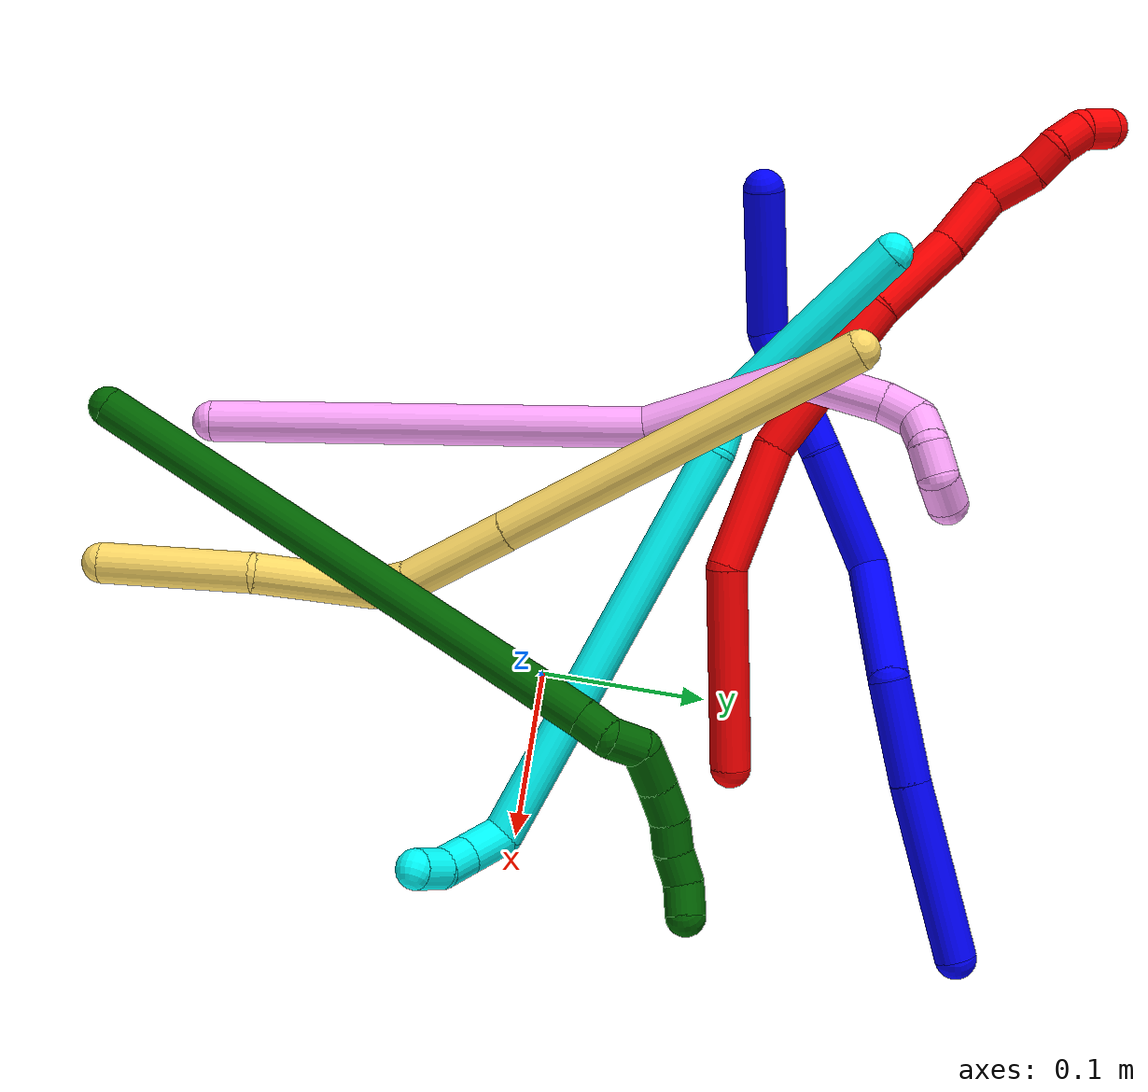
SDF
<sdf version="1.7">
 <world name="default">
  <plugin name="TubeGeneratorPlugin" filename="libtube_generator_plugin.so"/>
  <model name="photoneo_s_sensor">
   <static>1</static>
   <pose>0 0 2 1.57079 1.57079 3.14159</pose>
   <link name="link">
    <inertial><mass>0.1</mass></inertial>
    <sensor name="sensor" type="depth">
     <update_rate>30</update_rate>
     <camera>
      <horizontal_fov>1.22</horizontal_fov>
      <image><width>1920</width><height>1200</height><format>B8G8R8</format></image>
      <clip><near>0.1</near><far>4</far></clip>
      <depth_camera><output>points</output></depth_camera>
     </camera>
     <plugin name="camera_plugin" filename="libgazebo_ros_depth_camera.so">
      <baseline>0.2</baseline>
      <alwaysOn>1</alwaysOn>
      <updateRate>0.0</updateRate>
      <cameraName>camera_ir</cameraName>
      <imageTopicName>/camera/color/image_raw</imageTopicName>
      <cameraInfoTopicName>/camera/color/camera_info</cameraInfoTopicName>
      <depthImageTopicName>/camera/depth/image_raw</depthImageTopicName>
      <depthImageCameraInfoTopicName>/camera/depth/camera_info</depthImageCameraInfoTopicName>
      <pointCloudTopicName>/camera/depth/points</pointCloudTopicName>
      <frameName>fr_optical</frameName>
      <pointCloudCutoff>0.1</pointCloudCutoff>
      <pointCloudCutoffMax>2.0</pointCloudCutoffMax>
      <distortionK1>0</distortionK1>
      <distortionK2>0</distortionK2>
      <distortionK3>0</distortionK3>
      <distortionT1>0</distortionT1>
      <distortionT2>0</distortionT2>
      <CxPrime>0</CxPrime>
      <Cx>0</Cx>
      <Cy>0</Cy>
      <focalLength>0</focalLength>
      <hackBaseline>0</hackBaseline>
     </plugin>
    </sensor>
   </link>
  </model>
  <gravity>0 0 -9.8</gravity>
  <magnetic_field>6e-06 2.3e-05 -4.2e-05</magnetic_field>
  <atmosphere type="adiabatic"/>
  <physics name="default_physics" default="0" type="ode">
   <max_step_size>0.003</max_step_size>
   <real_time_factor>1</real_time_factor>
   <real_time_update_rate>1000</real_time_update_rate>
   <max_contacts>10000</max_contacts>
   <ode>
    <solver>
     <type>quick</type>
     <iters>100</iters>
     <sor>1.3</sor>
     <use_dynamic_moi_rescaling>0</use_dynamic_moi_rescaling>
    </solver>
    <constraints>
     <contact_max_correcting_vel>0</contact_max_correcting_vel>
     <contact_surface_layer>0.001</contact_surface_layer>
     <cfm>0</cfm>
     <erp>0.2</erp>
    </constraints>
   </ode>
  </physics>
  <scene><ambient>0.4 0.4 0.4 1</ambient><background>0.7 0.7 0.7 1</background><shadows>0</shadows></scene>
  <audio><device>default</device></audio>
  <spherical_coordinates>
   <surface_model>EARTH_WGS84</surface_model>
   <latitude_deg>0</latitude_deg>
   <longitude_deg>0</longitude_deg>
   <elevation>0</elevation>
   <heading_deg>0</heading_deg>
  </spherical_coordinates>
  <model name="bin">
   <static>1</static>
   <link name="bottom">
    <collision name="collision-bottom">
     <pose>0 0 -0.01 0 -0 0</pose>
     <geometry><box><size>0.8 0.6 0.02</size></box></geometry>
     <surface>
      <friction><ode><mu>100</mu><mu2>100</mu2></ode></friction>
      <contact><collide_bitmask>65535</collide_bitmask></contact>
     </surface>
    </collision>
   </link>
   <link name="west_wall">
    <collision name="collision-west_wall">
     <pose>-0.41 0 0.1 0 -0 0</pose>
     <geometry><box><size>0.02 0.6 0.2</size></box></geometry>
     <surface>
      <friction><ode><mu>100</mu><mu2>100</mu2></ode></friction>
      <contact><collide_bitmask>65535</collide_bitmask></contact>
     </surface>
    </collision>
   </link>
   <link name="east_wall">
    <collision name="collision-east_wall">
     <pose>0.41 0 0.1 0 -0 0</pose>
     <geometry><box><size>0.02 0.6 0.2</size></box></geometry>
     <surface>
      <friction><ode><mu>100</mu><mu2>100</mu2></ode></friction>
      <contact><collide_bitmask>65535</collide_bitmask></contact>
     </surface>
    </collision>
   </link>
   <link name="south_wall">
    <collision name="collision-south_wall">
     <pose>0 -0.31 0.1 0 -0 0</pose>
     <geometry><box><size>0.8 0.02 0.2</size></box></geometry>
     <surface>
      <friction><ode><mu>100</mu><mu2>100</mu2></ode></friction>
      <contact><collide_bitmask>65535</collide_bitmask></contact>
     </surface>
    </collision>
   </link>
   <link name="north_wall">
    <collision name="collision-north_wall">
     <pose>0 0.31 0.1 0 -0 0</pose>
     <geometry><box><size>0.8 0.02 0.2</size></box></geometry>
     <surface>
      <friction><ode><mu>100</mu><mu2>100</mu2></ode></friction>
      <contact><collide_bitmask>65535</collide_bitmask></contact>
     </surface>
    </collision>
   </link>
  </model>
  <model name="1">
   <static>0</static>
   <link name="1">
    <collision name="collision-cylinder-e_1_1_4">
     <pose>-0.023492 -0.013663 -0.047147 2.85952 -0.446362 -2.02357</pose>
     <geometry><cylinder><radius>0.0125</radius><length>0.108837</length></cylinder></geometry>
     <surface>
      <friction><ode><mu>1.16</mu><mu2>1.16</mu2><slip1>0</slip1><slip2>0</slip2></ode></friction>
      <contact><ode><kp>1e+06</kp><kd>1</kd><max_vel>0</max_vel><min_depth>0.001</min_depth></ode></contact>
     </surface>
    </collision>
    <visual name="visual-cylinder-e_1_1_4">
     <pose>-0.023492 -0.013663 -0.047147 2.85952 -0.446362 -2.02357</pose>
     <geometry><cylinder><radius>0.0125</radius><length>0.108837</length></cylinder></geometry>
     <material><ambient>0 0 1 1</ambient></material>
    </visual>
    <collision name="collision-cylinder-e_2_4_5">
     <pose>-0.059823 -0.03661 -0.121325 2.81079 -0.422219 -1.81807</pose>
     <geometry><cylinder><radius>0.0125</radius><length>0.062667</length></cylinder></geometry>
     <surface>
      <friction><ode><mu>1.16</mu><mu2>1.16</mu2><slip1>0</slip1><slip2>0</slip2></ode></friction>
      <contact><ode><kp>1e+06</kp><kd>1</kd><max_vel>0</max_vel><min_depth>0.001</min_depth></ode></contact>
     </surface>
    </collision>
    <visual name="visual-cylinder-e_2_4_5">
     <pose>-0.059823 -0.03661 -0.121325 2.81079 -0.422219 -1.81807</pose>
     <geometry><cylinder><radius>0.0125</radius><length>0.062667</length></cylinder></geometry>
     <material><ambient>0 0 1 1</ambient></material>
    </visual>
    <collision name="collision-cylinder-e_3_5_6">
     <pose>-0.100586 -0.072873 -0.162557 2.05525 -0.741507 -1.1441</pose>
     <geometry><cylinder><radius>0.0125</radius><length>0.082685</length></cylinder></geometry>
     <surface>
      <friction><ode><mu>1.16</mu><mu2>1.16</mu2><slip1>0</slip1><slip2>0</slip2></ode></friction>
      <contact><ode><kp>1e+06</kp><kd>1</kd><max_vel>0</max_vel><min_depth>0.001</min_depth></ode></contact>
     </surface>
    </collision>
    <visual name="visual-cylinder-e_3_5_6">
     <pose>-0.100586 -0.072873 -0.162557 2.05525 -0.741507 -1.1441</pose>
     <geometry><cylinder><radius>0.0125</radius><length>0.082685</length></cylinder></geometry>
     <material><ambient>0 0 1 1</ambient></material>
    </visual>
    <collision name="collision-cylinder-e_4_6_7">
     <pose>-0.148546 -0.105651 -0.208865 2.96294 -0.550718 -2.52764</pose>
     <geometry><cylinder><radius>0.0125</radius><length>0.07658</length></cylinder></geometry>
     <surface>
      <friction><ode><mu>1.16</mu><mu2>1.16</mu2><slip1>0</slip1><slip2>0</slip2></ode></friction>
      <contact><ode><kp>1e+06</kp><kd>1</kd><max_vel>0</max_vel><min_depth>0.001</min_depth></ode></contact>
     </surface>
    </collision>
    <visual name="visual-cylinder-e_4_6_7">
     <pose>-0.148546 -0.105651 -0.208865 2.96294 -0.550718 -2.52764</pose>
     <geometry><cylinder><radius>0.0125</radius><length>0.07658</length></cylinder></geometry>
     <material><ambient>0 0 1 1</ambient></material>
    </visual>
    <collision name="collision-cylinder-e_5_7_8">
     <pose>-0.193655 -0.120429 -0.271124 2.85211 -0.672905 -2.35187</pose>
     <geometry><cylinder><radius>0.0125</radius><length>0.080456</length></cylinder></geometry>
     <surface>
      <friction><ode><mu>1.16</mu><mu2>1.16</mu2><slip1>0</slip1><slip2>0</slip2></ode></friction>
      <contact><ode><kp>1e+06</kp><kd>1</kd><max_vel>0</max_vel><min_depth>0.001</min_depth></ode></contact>
     </surface>
    </collision>
    <visual name="visual-cylinder-e_5_7_8">
     <pose>-0.193655 -0.120429 -0.271124 2.85211 -0.672905 -2.35187</pose>
     <geometry><cylinder><radius>0.0125</radius><length>0.080456</length></cylinder></geometry>
     <material><ambient>0 0 1 1</ambient></material>
    </visual>
    <collision name="collision-cylinder-e_6_8_2">
     <pose>-0.22276 -0.138937 -0.34444 2.92435 -0.090961 -0.79074</pose>
     <geometry><cylinder><radius>0.0125</radius><length>0.088776</length></cylinder></geometry>
     <surface>
      <friction><ode><mu>1.16</mu><mu2>1.16</mu2><slip1>0</slip1><slip2>0</slip2></ode></friction>
      <contact><ode><kp>1e+06</kp><kd>1</kd><max_vel>0</max_vel><min_depth>0.001</min_depth></ode></contact>
     </surface>
    </collision>
    <visual name="visual-cylinder-e_6_8_2">
     <pose>-0.22276 -0.138937 -0.34444 2.92435 -0.090961 -0.79074</pose>
     <geometry><cylinder><radius>0.0125</radius><length>0.088776</length></cylinder></geometry>
     <material><ambient>0 0 1 1</ambient></material>
    </visual>
    <collision name="collision-sphere-2">
     <pose>-0.226792 -0.148464 -0.387606 0 -0 0</pose>
     <geometry><sphere><radius>0.0125</radius></sphere></geometry>
     <surface>
      <friction><ode><mu>1.16</mu><mu2>1.16</mu2><slip1>0</slip1><slip2>0</slip2></ode></friction>
      <contact><ode><kp>1e+06</kp><kd>1</kd><max_vel>0</max_vel><min_depth>0.001</min_depth></ode></contact>
     </surface>
    </collision>
    <visual name="visual-sphere-2">
     <pose>-0.226792 -0.148464 -0.387606 0 -0 0</pose>
     <geometry><sphere><radius>0.0125</radius></sphere></geometry>
     <material><ambient>0 0 1 1</ambient></material>
    </visual>
    <collision name="collision-sphere-4">
     <pose>-0.046983 -0.027327 -0.094293 0 -0 0</pose>
     <geometry><sphere><radius>0.0125</radius></sphere></geometry>
     <surface>
      <friction><ode><mu>1.16</mu><mu2>1.16</mu2><slip1>0</slip1><slip2>0</slip2></ode></friction>
      <contact><ode><kp>1e+06</kp><kd>1</kd><max_vel>0</max_vel><min_depth>0.001</min_depth></ode></contact>
     </surface>
    </collision>
    <visual name="visual-sphere-4">
     <pose>-0.046983 -0.027327 -0.094293 0 -0 0</pose>
     <geometry><sphere><radius>0.0125</radius></sphere></geometry>
     <material><ambient>0 0 1 1</ambient></material>
    </visual>
    <collision name="collision-sphere-1">
     <geometry><sphere><radius>0.0125</radius></sphere></geometry>
     <surface>
      <friction><ode><mu>1.16</mu><mu2>1.16</mu2><slip1>0</slip1><slip2>0</slip2></ode></friction>
      <contact><ode><kp>1e+06</kp><kd>1</kd><max_vel>0</max_vel><min_depth>0.001</min_depth></ode></contact>
     </surface>
    </collision>
    <visual name="visual-sphere-1">
     <geometry><sphere><radius>0.0125</radius></sphere></geometry>
     <material><ambient>0 0 1 1</ambient></material>
    </visual>
    <collision name="collision-sphere-8">
     <pose>-0.218728 -0.129409 -0.301274 0 -0 0</pose>
     <geometry><sphere><radius>0.0125</radius></sphere></geometry>
     <surface>
      <friction><ode><mu>1.16</mu><mu2>1.16</mu2><slip1>0</slip1><slip2>0</slip2></ode></friction>
      <contact><ode><kp>1e+06</kp><kd>1</kd><max_vel>0</max_vel><min_depth>0.001</min_depth></ode></contact>
     </surface>
    </collision>
    <visual name="visual-sphere-8">
     <pose>-0.218728 -0.129409 -0.301274 0 -0 0</pose>
     <geometry><sphere><radius>0.0125</radius></sphere></geometry>
     <material><ambient>0 0 1 1</ambient></material>
    </visual>
    <collision name="collision-sphere-5">
     <pose>-0.072663 -0.045893 -0.148357 0 -0 0</pose>
     <geometry><sphere><radius>0.0125</radius></sphere></geometry>
     <surface>
      <friction><ode><mu>1.16</mu><mu2>1.16</mu2><slip1>0</slip1><slip2>0</slip2></ode></friction>
      <contact><ode><kp>1e+06</kp><kd>1</kd><max_vel>0</max_vel><min_depth>0.001</min_depth></ode></contact>
     </surface>
    </collision>
    <visual name="visual-sphere-5">
     <pose>-0.072663 -0.045893 -0.148357 0 -0 0</pose>
     <geometry><sphere><radius>0.0125</radius></sphere></geometry>
     <material><ambient>0 0 1 1</ambient></material>
    </visual>
    <collision name="collision-sphere-6">
     <pose>-0.128508 -0.099853 -0.176756 0 -0 0</pose>
     <geometry><sphere><radius>0.0125</radius></sphere></geometry>
     <surface>
      <friction><ode><mu>1.16</mu><mu2>1.16</mu2><slip1>0</slip1><slip2>0</slip2></ode></friction>
      <contact><ode><kp>1e+06</kp><kd>1</kd><max_vel>0</max_vel><min_depth>0.001</min_depth></ode></contact>
     </surface>
    </collision>
    <visual name="visual-sphere-6">
     <pose>-0.128508 -0.099853 -0.176756 0 -0 0</pose>
     <geometry><sphere><radius>0.0125</radius></sphere></geometry>
     <material><ambient>0 0 1 1</ambient></material>
    </visual>
    <collision name="collision-sphere-7">
     <pose>-0.168583 -0.111449 -0.240975 0 -0 0</pose>
     <geometry><sphere><radius>0.0125</radius></sphere></geometry>
     <surface>
      <friction><ode><mu>1.16</mu><mu2>1.16</mu2><slip1>0</slip1><slip2>0</slip2></ode></friction>
      <contact><ode><kp>1e+06</kp><kd>1</kd><max_vel>0</max_vel><min_depth>0.001</min_depth></ode></contact>
     </surface>
    </collision>
    <visual name="visual-sphere-7">
     <pose>-0.168583 -0.111449 -0.240975 0 -0 0</pose>
     <geometry><sphere><radius>0.0125</radius></sphere></geometry>
     <material><ambient>0 0 1 1</ambient></material>
    </visual>
    <inertial>
     <pose>-0.122709 -0.079842 -0.189124 0 -0 0</pose>
     <mass>0.5</mass>
     <inertia>
      <ixx>-0.000296</ixx>
      <ixy>0</ixy>
      <ixz>0</ixz>
      <iyy>-0.00013</iyy>
      <iyz>0</iyz>
      <izz>0.000215</izz>
     </inertia>
    </inertial>
   </link>
   <pose>0.126479 0.270489 0.042701 2.39323 -0.667683 1.31028</pose>
  </model>
  <model name="2">
   <static>0</static>
   <link name="2">
    <collision name="collision-cylinder-e_1_1_4">
     <pose>-0.004161 -0.006115 0.061323 0.099397 -0.067417 -0.003355</pose>
     <geometry><cylinder><radius>0.0125</radius><length>0.123535</length></cylinder></geometry>
     <surface>
      <friction><ode><mu>1.16</mu><mu2>1.16</mu2><slip1>0</slip1><slip2>0</slip2></ode></friction>
      <contact><ode><kp>1e+06</kp><kd>1</kd><max_vel>0</max_vel><min_depth>0.001</min_depth></ode></contact>
     </surface>
    </collision>
    <visual name="visual-cylinder-e_1_1_4">
     <pose>-0.004161 -0.006115 0.061323 0.099397 -0.067417 -0.003355</pose>
     <geometry><cylinder><radius>0.0125</radius><length>0.123535</length></cylinder></geometry>
     <material><ambient>1 0 0 1</ambient></material>
    </visual>
    <collision name="collision-cylinder-e_2_4_5">
     <pose>-0.01463 0.001521 0.158613 -0.365203 -0.16237 0.030047</pose>
     <geometry><cylinder><radius>0.0125</radius><length>0.078039</length></cylinder></geometry>
     <surface>
      <friction><ode><mu>1.16</mu><mu2>1.16</mu2><slip1>0</slip1><slip2>0</slip2></ode></friction>
      <contact><ode><kp>1e+06</kp><kd>1</kd><max_vel>0</max_vel><min_depth>0.001</min_depth></ode></contact>
     </surface>
    </collision>
    <visual name="visual-cylinder-e_2_4_5">
     <pose>-0.01463 0.001521 0.158613 -0.365203 -0.16237 0.030047</pose>
     <geometry><cylinder><radius>0.0125</radius><length>0.078039</length></cylinder></geometry>
     <material><ambient>1 0 0 1</ambient></material>
    </visual>
    <collision name="collision-cylinder-e_3_5_6">
     <pose>-0.019731 0.029073 0.215886 -0.574736 0.047482 -0.014036</pose>
     <geometry><cylinder><radius>0.0125</radius><length>0.050827</length></cylinder></geometry>
     <surface>
      <friction><ode><mu>1.16</mu><mu2>1.16</mu2><slip1>0</slip1><slip2>0</slip2></ode></friction>
      <contact><ode><kp>1e+06</kp><kd>1</kd><max_vel>0</max_vel><min_depth>0.001</min_depth></ode></contact>
     </surface>
    </collision>
    <visual name="visual-cylinder-e_3_5_6">
     <pose>-0.019731 0.029073 0.215886 -0.574736 0.047482 -0.014036</pose>
     <geometry><cylinder><radius>0.0125</radius><length>0.050827</length></cylinder></geometry>
     <material><ambient>1 0 0 1</ambient></material>
    </visual>
    <collision name="collision-cylinder-e_4_6_7">
     <pose>-0.019772 0.059257 0.259628 -0.63079 -0.044858 0.014639</pose>
     <geometry><cylinder><radius>0.0125</radius><length>0.055618</length></cylinder></geometry>
     <surface>
      <friction><ode><mu>1.16</mu><mu2>1.16</mu2><slip1>0</slip1><slip2>0</slip2></ode></friction>
      <contact><ode><kp>1e+06</kp><kd>1</kd><max_vel>0</max_vel><min_depth>0.001</min_depth></ode></contact>
     </surface>
    </collision>
    <visual name="visual-cylinder-e_4_6_7">
     <pose>-0.019772 0.059257 0.259628 -0.63079 -0.044858 0.014639</pose>
     <geometry><cylinder><radius>0.0125</radius><length>0.055618</length></cylinder></geometry>
     <material><ambient>1 0 0 1</ambient></material>
    </visual>
    <collision name="collision-cylinder-e_5_7_8">
     <pose>-0.025123 0.097487 0.301257 -0.849891 -0.14019 0.063521</pose>
     <geometry><cylinder><radius>0.0125</radius><length>0.058735</length></cylinder></geometry>
     <surface>
      <friction><ode><mu>1.16</mu><mu2>1.16</mu2><slip1>0</slip1><slip2>0</slip2></ode></friction>
      <contact><ode><kp>1e+06</kp><kd>1</kd><max_vel>0</max_vel><min_depth>0.001</min_depth></ode></contact>
     </surface>
    </collision>
    <visual name="visual-cylinder-e_5_7_8">
     <pose>-0.025123 0.097487 0.301257 -0.849891 -0.14019 0.063521</pose>
     <geometry><cylinder><radius>0.0125</radius><length>0.058735</length></cylinder></geometry>
     <material><ambient>1 0 0 1</ambient></material>
    </visual>
    <collision name="collision-cylinder-e_6_8_9">
     <pose>-0.032716 0.132699 0.335809 -0.71623 -0.16976 0.063665</pose>
     <geometry><cylinder><radius>0.0125</radius><length>0.041316</length></cylinder></geometry>
     <surface>
      <friction><ode><mu>1.16</mu><mu2>1.16</mu2><slip1>0</slip1><slip2>0</slip2></ode></friction>
      <contact><ode><kp>1e+06</kp><kd>1</kd><max_vel>0</max_vel><min_depth>0.001</min_depth></ode></contact>
     </surface>
    </collision>
    <visual name="visual-cylinder-e_6_8_9">
     <pose>-0.032716 0.132699 0.335809 -0.71623 -0.16976 0.063665</pose>
     <geometry><cylinder><radius>0.0125</radius><length>0.041316</length></cylinder></geometry>
     <material><ambient>1 0 0 1</ambient></material>
    </visual>
    <collision name="collision-cylinder-e_7_9_10">
     <pose>-0.033309 0.158698 0.359778 -0.972424 0.187315 -0.099211</pose>
     <geometry><cylinder><radius>0.0125</radius><length>0.031117</length></cylinder></geometry>
     <surface>
      <friction><ode><mu>1.16</mu><mu2>1.16</mu2><slip1>0</slip1><slip2>0</slip2></ode></friction>
      <contact><ode><kp>1e+06</kp><kd>1</kd><max_vel>0</max_vel><min_depth>0.001</min_depth></ode></contact>
     </surface>
    </collision>
    <visual name="visual-cylinder-e_7_9_10">
     <pose>-0.033309 0.158698 0.359778 -0.972424 0.187315 -0.099211</pose>
     <geometry><cylinder><radius>0.0125</radius><length>0.031117</length></cylinder></geometry>
     <material><ambient>1 0 0 1</ambient></material>
    </visual>
    <collision name="collision-cylinder-e_8_10_11">
     <pose>-0.02835 0.177334 0.376495 -0.637687 0.201627 -0.06676</pose>
     <geometry><cylinder><radius>0.0125</radius><length>0.020594</length></cylinder></geometry>
     <surface>
      <friction><ode><mu>1.16</mu><mu2>1.16</mu2><slip1>0</slip1><slip2>0</slip2></ode></friction>
      <contact><ode><kp>1e+06</kp><kd>1</kd><max_vel>0</max_vel><min_depth>0.001</min_depth></ode></contact>
     </surface>
    </collision>
    <visual name="visual-cylinder-e_8_10_11">
     <pose>-0.02835 0.177334 0.376495 -0.637687 0.201627 -0.06676</pose>
     <geometry><cylinder><radius>0.0125</radius><length>0.020594</length></cylinder></geometry>
     <material><ambient>1 0 0 1</ambient></material>
    </visual>
    <collision name="collision-cylinder-e_9_11_12">
     <pose>-0.026741 0.191597 0.390392 -0.959165 -0.044941 0.023376</pose>
     <geometry><cylinder><radius>0.0125</radius><length>0.020191</length></cylinder></geometry>
     <surface>
      <friction><ode><mu>1.16</mu><mu2>1.16</mu2><slip1>0</slip1><slip2>0</slip2></ode></friction>
      <contact><ode><kp>1e+06</kp><kd>1</kd><max_vel>0</max_vel><min_depth>0.001</min_depth></ode></contact>
     </surface>
    </collision>
    <visual name="visual-cylinder-e_9_11_12">
     <pose>-0.026741 0.191597 0.390392 -0.959165 -0.044941 0.023376</pose>
     <geometry><cylinder><radius>0.0125</radius><length>0.020191</length></cylinder></geometry>
     <material><ambient>1 0 0 1</ambient></material>
    </visual>
    <collision name="collision-cylinder-e_10_12_2">
     <pose>-0.028937 0.209674 0.397081 -1.47961 -0.174923 0.159727</pose>
     <geometry><cylinder><radius>0.0125</radius><length>0.020027</length></cylinder></geometry>
     <surface>
      <friction><ode><mu>1.16</mu><mu2>1.16</mu2><slip1>0</slip1><slip2>0</slip2></ode></friction>
      <contact><ode><kp>1e+06</kp><kd>1</kd><max_vel>0</max_vel><min_depth>0.001</min_depth></ode></contact>
     </surface>
    </collision>
    <visual name="visual-cylinder-e_10_12_2">
     <pose>-0.028937 0.209674 0.397081 -1.47961 -0.174923 0.159727</pose>
     <geometry><cylinder><radius>0.0125</radius><length>0.020027</length></cylinder></geometry>
     <material><ambient>1 0 0 1</ambient></material>
    </visual>
    <collision name="collision-sphere-2">
     <pose>-0.03068 0.219494 0.397979 0 -0 0</pose>
     <geometry><sphere><radius>0.0125</radius></sphere></geometry>
     <surface>
      <friction><ode><mu>1.16</mu><mu2>1.16</mu2><slip1>0</slip1><slip2>0</slip2></ode></friction>
      <contact><ode><kp>1e+06</kp><kd>1</kd><max_vel>0</max_vel><min_depth>0.001</min_depth></ode></contact>
     </surface>
    </collision>
    <visual name="visual-sphere-2">
     <pose>-0.03068 0.219494 0.397979 0 -0 0</pose>
     <geometry><sphere><radius>0.0125</radius></sphere></geometry>
     <material><ambient>1 0 0 1</ambient></material>
    </visual>
    <collision name="collision-sphere-12">
     <pose>-0.027195 0.199854 0.396183 0 -0 0</pose>
     <geometry><sphere><radius>0.0125</radius></sphere></geometry>
     <surface>
      <friction><ode><mu>1.16</mu><mu2>1.16</mu2><slip1>0</slip1><slip2>0</slip2></ode></friction>
      <contact><ode><kp>1e+06</kp><kd>1</kd><max_vel>0</max_vel><min_depth>0.001</min_depth></ode></contact>
     </surface>
    </collision>
    <visual name="visual-sphere-12">
     <pose>-0.027195 0.199854 0.396183 0 -0 0</pose>
     <geometry><sphere><radius>0.0125</radius></sphere></geometry>
     <material><ambient>1 0 0 1</ambient></material>
    </visual>
    <collision name="collision-sphere-11">
     <pose>-0.026288 0.18334 0.384601 0 -0 0</pose>
     <geometry><sphere><radius>0.0125</radius></sphere></geometry>
     <surface>
      <friction><ode><mu>1.16</mu><mu2>1.16</mu2><slip1>0</slip1><slip2>0</slip2></ode></friction>
      <contact><ode><kp>1e+06</kp><kd>1</kd><max_vel>0</max_vel><min_depth>0.001</min_depth></ode></contact>
     </surface>
    </collision>
    <visual name="visual-sphere-11">
     <pose>-0.026288 0.18334 0.384601 0 -0 0</pose>
     <geometry><sphere><radius>0.0125</radius></sphere></geometry>
     <material><ambient>1 0 0 1</ambient></material>
    </visual>
    <collision name="collision-sphere-10">
     <pose>-0.030412 0.171328 0.368389 0 -0 0</pose>
     <geometry><sphere><radius>0.0125</radius></sphere></geometry>
     <surface>
      <friction><ode><mu>1.16</mu><mu2>1.16</mu2><slip1>0</slip1><slip2>0</slip2></ode></friction>
      <contact><ode><kp>1e+06</kp><kd>1</kd><max_vel>0</max_vel><min_depth>0.001</min_depth></ode></contact>
     </surface>
    </collision>
    <visual name="visual-sphere-10">
     <pose>-0.030412 0.171328 0.368389 0 -0 0</pose>
     <geometry><sphere><radius>0.0125</radius></sphere></geometry>
     <material><ambient>1 0 0 1</ambient></material>
    </visual>
    <collision name="collision-sphere-9">
     <pose>-0.036207 0.146067 0.351167 0 -0 0</pose>
     <geometry><sphere><radius>0.0125</radius></sphere></geometry>
     <surface>
      <friction><ode><mu>1.16</mu><mu2>1.16</mu2><slip1>0</slip1><slip2>0</slip2></ode></friction>
      <contact><ode><kp>1e+06</kp><kd>1</kd><max_vel>0</max_vel><min_depth>0.001</min_depth></ode></contact>
     </surface>
    </collision>
    <visual name="visual-sphere-9">
     <pose>-0.036207 0.146067 0.351167 0 -0 0</pose>
     <geometry><sphere><radius>0.0125</radius></sphere></geometry>
     <material><ambient>1 0 0 1</ambient></material>
    </visual>
    <collision name="collision-sphere-4">
     <pose>-0.008322 -0.012231 0.122646 0 -0 0</pose>
     <geometry><sphere><radius>0.0125</radius></sphere></geometry>
     <surface>
      <friction><ode><mu>1.16</mu><mu2>1.16</mu2><slip1>0</slip1><slip2>0</slip2></ode></friction>
      <contact><ode><kp>1e+06</kp><kd>1</kd><max_vel>0</max_vel><min_depth>0.001</min_depth></ode></contact>
     </surface>
    </collision>
    <visual name="visual-sphere-4">
     <pose>-0.008322 -0.012231 0.122646 0 -0 0</pose>
     <geometry><sphere><radius>0.0125</radius></sphere></geometry>
     <material><ambient>1 0 0 1</ambient></material>
    </visual>
    <collision name="collision-sphere-1">
     <geometry><sphere><radius>0.0125</radius></sphere></geometry>
     <surface>
      <friction><ode><mu>1.16</mu><mu2>1.16</mu2><slip1>0</slip1><slip2>0</slip2></ode></friction>
      <contact><ode><kp>1e+06</kp><kd>1</kd><max_vel>0</max_vel><min_depth>0.001</min_depth></ode></contact>
     </surface>
    </collision>
    <visual name="visual-sphere-1">
     <geometry><sphere><radius>0.0125</radius></sphere></geometry>
     <material><ambient>1 0 0 1</ambient></material>
    </visual>
    <collision name="collision-sphere-8">
     <pose>-0.029226 0.119331 0.320451 0 -0 0</pose>
     <geometry><sphere><radius>0.0125</radius></sphere></geometry>
     <surface>
      <friction><ode><mu>1.16</mu><mu2>1.16</mu2><slip1>0</slip1><slip2>0</slip2></ode></friction>
      <contact><ode><kp>1e+06</kp><kd>1</kd><max_vel>0</max_vel><min_depth>0.001</min_depth></ode></contact>
     </surface>
    </collision>
    <visual name="visual-sphere-8">
     <pose>-0.029226 0.119331 0.320451 0 -0 0</pose>
     <geometry><sphere><radius>0.0125</radius></sphere></geometry>
     <material><ambient>1 0 0 1</ambient></material>
    </visual>
    <collision name="collision-sphere-5">
     <pose>-0.020938 0.015273 0.19458 0 -0 0</pose>
     <geometry><sphere><radius>0.0125</radius></sphere></geometry>
     <surface>
      <friction><ode><mu>1.16</mu><mu2>1.16</mu2><slip1>0</slip1><slip2>0</slip2></ode></friction>
      <contact><ode><kp>1e+06</kp><kd>1</kd><max_vel>0</max_vel><min_depth>0.001</min_depth></ode></contact>
     </surface>
    </collision>
    <visual name="visual-sphere-5">
     <pose>-0.020938 0.015273 0.19458 0 -0 0</pose>
     <geometry><sphere><radius>0.0125</radius></sphere></geometry>
     <material><ambient>1 0 0 1</ambient></material>
    </visual>
    <collision name="collision-sphere-6">
     <pose>-0.018525 0.042872 0.237193 0 -0 0</pose>
     <geometry><sphere><radius>0.0125</radius></sphere></geometry>
     <surface>
      <friction><ode><mu>1.16</mu><mu2>1.16</mu2><slip1>0</slip1><slip2>0</slip2></ode></friction>
      <contact><ode><kp>1e+06</kp><kd>1</kd><max_vel>0</max_vel><min_depth>0.001</min_depth></ode></contact>
     </surface>
    </collision>
    <visual name="visual-sphere-6">
     <pose>-0.018525 0.042872 0.237193 0 -0 0</pose>
     <geometry><sphere><radius>0.0125</radius></sphere></geometry>
     <material><ambient>1 0 0 1</ambient></material>
    </visual>
    <collision name="collision-sphere-7">
     <pose>-0.021019 0.075642 0.282063 0 -0 0</pose>
     <geometry><sphere><radius>0.0125</radius></sphere></geometry>
     <surface>
      <friction><ode><mu>1.16</mu><mu2>1.16</mu2><slip1>0</slip1><slip2>0</slip2></ode></friction>
      <contact><ode><kp>1e+06</kp><kd>1</kd><max_vel>0</max_vel><min_depth>0.001</min_depth></ode></contact>
     </surface>
    </collision>
    <visual name="visual-sphere-7">
     <pose>-0.021019 0.075642 0.282063 0 -0 0</pose>
     <geometry><sphere><radius>0.0125</radius></sphere></geometry>
     <material><ambient>1 0 0 1</ambient></material>
    </visual>
    <inertial>
     <pose>-0.018651 0.064006 0.223438 0 -0 0</pose>
     <mass>0.5</mass>
     <inertia>
      <ixx>0.000267</ixx>
      <ixy>0</ixy>
      <ixz>0</ixz>
      <iyy>0.000267</iyy>
      <iyz>0</iyz>
      <izz>1.1e-05</izz>
     </inertia>
    </inertial>
   </link>
   <pose>0.037518 0.122286 0.012545 -0.918209 -1.1459 1.03404</pose>
  </model>
  <model name="3">
   <static>0</static>
   <link name="3">
    <collision name="collision-cylinder-e_1_1_4">
     <pose>0.048458 -0.018458 -0.042779 2.73425 0.805032 2.23828</pose>
     <geometry><cylinder><radius>0.0125</radius><length>0.134445</length></cylinder></geometry>
     <surface>
      <friction><ode><mu>1.16</mu><mu2>1.16</mu2><slip1>0</slip1><slip2>0</slip2></ode></friction>
      <contact><ode><kp>1e+06</kp><kd>1</kd><max_vel>0</max_vel><min_depth>0.001</min_depth></ode></contact>
     </surface>
    </collision>
    <visual name="visual-cylinder-e_1_1_4">
     <pose>0.048458 -0.018458 -0.042779 2.73425 0.805032 2.23828</pose>
     <geometry><cylinder><radius>0.0125</radius><length>0.134445</length></cylinder></geometry>
     <material><ambient>0.003922 1 0.996078 1</ambient></material>
    </visual>
    <collision name="collision-cylinder-e_2_4_5">
     <pose>0.098883 -0.039331 -0.100502 2.9814 0.129238 1.35697</pose>
     <geometry><cylinder><radius>0.0125</radius><length>0.030531</length></cylinder></geometry>
     <surface>
      <friction><ode><mu>1.16</mu><mu2>1.16</mu2><slip1>0</slip1><slip2>0</slip2></ode></friction>
      <contact><ode><kp>1e+06</kp><kd>1</kd><max_vel>0</max_vel><min_depth>0.001</min_depth></ode></contact>
     </surface>
    </collision>
    <visual name="visual-cylinder-e_2_4_5">
     <pose>0.098883 -0.039331 -0.100502 2.9814 0.129238 1.35697</pose>
     <geometry><cylinder><radius>0.0125</radius><length>0.030531</length></cylinder></geometry>
     <material><ambient>0.003922 1 0.996078 1</ambient></material>
    </visual>
    <collision name="collision-cylinder-e_3_5_6">
     <pose>0.156018 -0.080669 -0.22957 2.8129 0.429096 1.84047</pose>
     <geometry><cylinder><radius>0.0125</radius><length>0.265199</length></cylinder></geometry>
     <surface>
      <friction><ode><mu>1.16</mu><mu2>1.16</mu2><slip1>0</slip1><slip2>0</slip2></ode></friction>
      <contact><ode><kp>1e+06</kp><kd>1</kd><max_vel>0</max_vel><min_depth>0.001</min_depth></ode></contact>
     </surface>
    </collision>
    <visual name="visual-cylinder-e_3_5_6">
     <pose>0.156018 -0.080669 -0.22957 2.8129 0.429096 1.84047</pose>
     <geometry><cylinder><radius>0.0125</radius><length>0.265199</length></cylinder></geometry>
     <material><ambient>0.003922 1 0.996078 1</ambient></material>
    </visual>
    <collision name="collision-cylinder-e_4_6_7">
     <pose>0.217857 -0.113437 -0.354073 -2.60627 0.504969 -1.50975</pose>
     <geometry><cylinder><radius>0.0125</radius><length>0.027577</length></cylinder></geometry>
     <surface>
      <friction><ode><mu>1.16</mu><mu2>1.16</mu2><slip1>0</slip1><slip2>0</slip2></ode></friction>
      <contact><ode><kp>1e+06</kp><kd>1</kd><max_vel>0</max_vel><min_depth>0.001</min_depth></ode></contact>
     </surface>
    </collision>
    <visual name="visual-cylinder-e_4_6_7">
     <pose>0.217857 -0.113437 -0.354073 -2.60627 0.504969 -1.50975</pose>
     <geometry><cylinder><radius>0.0125</radius><length>0.027577</length></cylinder></geometry>
     <material><ambient>0.003922 1 0.996078 1</ambient></material>
    </visual>
    <collision name="collision-cylinder-e_5_7_8">
     <pose>0.22657 -0.09991 -0.372331 -2.38948 0.187066 -0.466502</pose>
     <geometry><cylinder><radius>0.0125</radius><length>0.021962</length></cylinder></geometry>
     <surface>
      <friction><ode><mu>1.16</mu><mu2>1.16</mu2><slip1>0</slip1><slip2>0</slip2></ode></friction>
      <contact><ode><kp>1e+06</kp><kd>1</kd><max_vel>0</max_vel><min_depth>0.001</min_depth></ode></contact>
     </surface>
    </collision>
    <visual name="visual-cylinder-e_5_7_8">
     <pose>0.22657 -0.09991 -0.372331 -2.38948 0.187066 -0.466502</pose>
     <geometry><cylinder><radius>0.0125</radius><length>0.021962</length></cylinder></geometry>
     <material><ambient>0.003922 1 0.996078 1</ambient></material>
    </visual>
    <collision name="collision-cylinder-e_6_8_2">
     <pose>0.231731 -0.083916 -0.384545 -2.03667 0.312605 -0.500517</pose>
     <geometry><cylinder><radius>0.0125</radius><length>0.020285</length></cylinder></geometry>
     <surface>
      <friction><ode><mu>1.16</mu><mu2>1.16</mu2><slip1>0</slip1><slip2>0</slip2></ode></friction>
      <contact><ode><kp>1e+06</kp><kd>1</kd><max_vel>0</max_vel><min_depth>0.001</min_depth></ode></contact>
     </surface>
    </collision>
    <visual name="visual-cylinder-e_6_8_2">
     <pose>0.231731 -0.083916 -0.384545 -2.03667 0.312605 -0.500517</pose>
     <geometry><cylinder><radius>0.0125</radius><length>0.020285</length></cylinder></geometry>
     <material><ambient>0.003922 1 0.996078 1</ambient></material>
    </visual>
    <collision name="collision-sphere-2">
     <pose>0.23485 -0.075294 -0.38888 0 -0 0</pose>
     <geometry><sphere><radius>0.0125</radius></sphere></geometry>
     <surface>
      <friction><ode><mu>1.16</mu><mu2>1.16</mu2><slip1>0</slip1><slip2>0</slip2></ode></friction>
      <contact><ode><kp>1e+06</kp><kd>1</kd><max_vel>0</max_vel><min_depth>0.001</min_depth></ode></contact>
     </surface>
    </collision>
    <visual name="visual-sphere-2">
     <pose>0.23485 -0.075294 -0.38888 0 -0 0</pose>
     <geometry><sphere><radius>0.0125</radius></sphere></geometry>
     <material><ambient>0.003922 1 0.996078 1</ambient></material>
    </visual>
    <collision name="collision-sphere-4">
     <pose>0.096915 -0.036916 -0.085558 0 -0 0</pose>
     <geometry><sphere><radius>0.0125</radius></sphere></geometry>
     <surface>
      <friction><ode><mu>1.16</mu><mu2>1.16</mu2><slip1>0</slip1><slip2>0</slip2></ode></friction>
      <contact><ode><kp>1e+06</kp><kd>1</kd><max_vel>0</max_vel><min_depth>0.001</min_depth></ode></contact>
     </surface>
    </collision>
    <visual name="visual-sphere-4">
     <pose>0.096915 -0.036916 -0.085558 0 -0 0</pose>
     <geometry><sphere><radius>0.0125</radius></sphere></geometry>
     <material><ambient>0.003922 1 0.996078 1</ambient></material>
    </visual>
    <collision name="collision-sphere-1">
     <geometry><sphere><radius>0.0125</radius></sphere></geometry>
     <surface>
      <friction><ode><mu>1.16</mu><mu2>1.16</mu2><slip1>0</slip1><slip2>0</slip2></ode></friction>
      <contact><ode><kp>1e+06</kp><kd>1</kd><max_vel>0</max_vel><min_depth>0.001</min_depth></ode></contact>
     </surface>
    </collision>
    <visual name="visual-sphere-1">
     <geometry><sphere><radius>0.0125</radius></sphere></geometry>
     <material><ambient>0.003922 1 0.996078 1</ambient></material>
    </visual>
    <collision name="collision-sphere-8">
     <pose>0.228612 -0.092539 -0.38021 0 -0 0</pose>
     <geometry><sphere><radius>0.0125</radius></sphere></geometry>
     <surface>
      <friction><ode><mu>1.16</mu><mu2>1.16</mu2><slip1>0</slip1><slip2>0</slip2></ode></friction>
      <contact><ode><kp>1e+06</kp><kd>1</kd><max_vel>0</max_vel><min_depth>0.001</min_depth></ode></contact>
     </surface>
    </collision>
    <visual name="visual-sphere-8">
     <pose>0.228612 -0.092539 -0.38021 0 -0 0</pose>
     <geometry><sphere><radius>0.0125</radius></sphere></geometry>
     <material><ambient>0.003922 1 0.996078 1</ambient></material>
    </visual>
    <collision name="collision-sphere-5">
     <pose>0.10085 -0.041746 -0.115446 0 -0 0</pose>
     <geometry><sphere><radius>0.0125</radius></sphere></geometry>
     <surface>
      <friction><ode><mu>1.16</mu><mu2>1.16</mu2><slip1>0</slip1><slip2>0</slip2></ode></friction>
      <contact><ode><kp>1e+06</kp><kd>1</kd><max_vel>0</max_vel><min_depth>0.001</min_depth></ode></contact>
     </surface>
    </collision>
    <visual name="visual-sphere-5">
     <pose>0.10085 -0.041746 -0.115446 0 -0 0</pose>
     <geometry><sphere><radius>0.0125</radius></sphere></geometry>
     <material><ambient>0.003922 1 0.996078 1</ambient></material>
    </visual>
    <collision name="collision-sphere-6">
     <pose>0.211186 -0.119593 -0.343693 0 -0 0</pose>
     <geometry><sphere><radius>0.0125</radius></sphere></geometry>
     <surface>
      <friction><ode><mu>1.16</mu><mu2>1.16</mu2><slip1>0</slip1><slip2>0</slip2></ode></friction>
      <contact><ode><kp>1e+06</kp><kd>1</kd><max_vel>0</max_vel><min_depth>0.001</min_depth></ode></contact>
     </surface>
    </collision>
    <visual name="visual-sphere-6">
     <pose>0.211186 -0.119593 -0.343693 0 -0 0</pose>
     <geometry><sphere><radius>0.0125</radius></sphere></geometry>
     <material><ambient>0.003922 1 0.996078 1</ambient></material>
    </visual>
    <collision name="collision-sphere-7">
     <pose>0.224528 -0.107281 -0.364452 0 -0 0</pose>
     <geometry><sphere><radius>0.0125</radius></sphere></geometry>
     <surface>
      <friction><ode><mu>1.16</mu><mu2>1.16</mu2><slip1>0</slip1><slip2>0</slip2></ode></friction>
      <contact><ode><kp>1e+06</kp><kd>1</kd><max_vel>0</max_vel><min_depth>0.001</min_depth></ode></contact>
     </surface>
    </collision>
    <visual name="visual-sphere-7">
     <pose>0.224528 -0.107281 -0.364452 0 -0 0</pose>
     <geometry><sphere><radius>0.0125</radius></sphere></geometry>
     <material><ambient>0.003922 1 0.996078 1</ambient></material>
    </visual>
    <inertial>
     <pose>0.133189 -0.064201 -0.190887 0 -0 0</pose>
     <mass>0.5</mass>
     <inertia>
      <ixx>0.001038</ixx>
      <ixy>0</ixy>
      <ixz>0</ixz>
      <iyy>0.002238</iyy>
      <iyz>0</iyz>
      <izz>-0.000321</izz>
     </inertia>
    </inertial>
   </link>
   <pose>-0.279703 0.165569 0.064031 2.04209 0.470087 -1.47</pose>
  </model>
  <model name="4">
   <static>0</static>
   <link name="4">
    <collision name="collision-cylinder-e_1_1_4">
     <pose>-0.008999 0.031477 0.128534 -0.240164 -0.067899 0.008196</pose>
     <geometry><cylinder><radius>0.0125</radius><length>0.265275</length></cylinder></geometry>
     <surface>
      <friction><ode><mu>1.16</mu><mu2>1.16</mu2><slip1>0</slip1><slip2>0</slip2></ode></friction>
      <contact><ode><kp>1e+06</kp><kd>1</kd><max_vel>0</max_vel><min_depth>0.001</min_depth></ode></contact>
     </surface>
    </collision>
    <visual name="visual-cylinder-e_1_1_4">
     <pose>-0.008999 0.031477 0.128534 -0.240164 -0.067899 0.008196</pose>
     <geometry><cylinder><radius>0.0125</radius><length>0.265275</length></cylinder></geometry>
     <material><ambient>1 0.65098 0.996078 1</ambient></material>
    </visual>
    <collision name="collision-cylinder-e_2_4_5">
     <pose>-0.017752 0.05748 0.306285 0.110766 0.004973 0.000276</pose>
     <geometry><cylinder><radius>0.0125</radius><length>0.099043</length></cylinder></geometry>
     <surface>
      <friction><ode><mu>1.16</mu><mu2>1.16</mu2><slip1>0</slip1><slip2>0</slip2></ode></friction>
      <contact><ode><kp>1e+06</kp><kd>1</kd><max_vel>0</max_vel><min_depth>0.001</min_depth></ode></contact>
     </surface>
    </collision>
    <visual name="visual-cylinder-e_2_4_5">
     <pose>-0.017752 0.05748 0.306285 0.110766 0.004973 0.000276</pose>
     <geometry><cylinder><radius>0.0125</radius><length>0.099043</length></cylinder></geometry>
     <material><ambient>1 0.65098 0.996078 1</ambient></material>
    </visual>
    <collision name="collision-cylinder-e_3_5_6">
     <pose>-0.017406 0.064275 0.377862 -0.501853 0.003916 -0.001004</pose>
     <geometry><cylinder><radius>0.0125</radius><length>0.05101</length></cylinder></geometry>
     <surface>
      <friction><ode><mu>1.16</mu><mu2>1.16</mu2><slip1>0</slip1><slip2>0</slip2></ode></friction>
      <contact><ode><kp>1e+06</kp><kd>1</kd><max_vel>0</max_vel><min_depth>0.001</min_depth></ode></contact>
     </surface>
    </collision>
    <visual name="visual-cylinder-e_3_5_6">
     <pose>-0.017406 0.064275 0.377862 -0.501853 0.003916 -0.001004</pose>
     <geometry><cylinder><radius>0.0125</radius><length>0.05101</length></cylinder></geometry>
     <material><ambient>1 0.65098 0.996078 1</ambient></material>
    </visual>
    <collision name="collision-cylinder-e_4_6_7">
     <pose>-0.013481 0.082584 0.409267 -0.58882 0.33816 -0.103434</pose>
     <geometry><cylinder><radius>0.0125</radius><length>0.023059</length></cylinder></geometry>
     <surface>
      <friction><ode><mu>1.16</mu><mu2>1.16</mu2><slip1>0</slip1><slip2>0</slip2></ode></friction>
      <contact><ode><kp>1e+06</kp><kd>1</kd><max_vel>0</max_vel><min_depth>0.001</min_depth></ode></contact>
     </surface>
    </collision>
    <visual name="visual-cylinder-e_4_6_7">
     <pose>-0.013481 0.082584 0.409267 -0.58882 0.33816 -0.103434</pose>
     <geometry><cylinder><radius>0.0125</radius><length>0.023059</length></cylinder></geometry>
     <material><ambient>1 0.65098 0.996078 1</ambient></material>
    </visual>
    <collision name="collision-cylinder-e_5_7_8">
     <pose>-0.000662 0.093975 0.420619 -1.16364 0.995977 -0.686903</pose>
     <geometry><cylinder><radius>0.0125</radius><length>0.021432</length></cylinder></geometry>
     <surface>
      <friction><ode><mu>1.16</mu><mu2>1.16</mu2><slip1>0</slip1><slip2>0</slip2></ode></friction>
      <contact><ode><kp>1e+06</kp><kd>1</kd><max_vel>0</max_vel><min_depth>0.001</min_depth></ode></contact>
     </surface>
    </collision>
    <visual name="visual-cylinder-e_5_7_8">
     <pose>-0.000662 0.093975 0.420619 -1.16364 0.995977 -0.686903</pose>
     <geometry><cylinder><radius>0.0125</radius><length>0.021432</length></cylinder></geometry>
     <material><ambient>1 0.65098 0.996078 1</ambient></material>
    </visual>
    <collision name="collision-cylinder-e_6_8_9">
     <pose>0.012633 0.108358 0.424085 -1.44322 0.441201 -0.389638</pose>
     <geometry><cylinder><radius>0.0125</radius><length>0.020144</length></cylinder></geometry>
     <surface>
      <friction><ode><mu>1.16</mu><mu2>1.16</mu2><slip1>0</slip1><slip2>0</slip2></ode></friction>
      <contact><ode><kp>1e+06</kp><kd>1</kd><max_vel>0</max_vel><min_depth>0.001</min_depth></ode></contact>
     </surface>
    </collision>
    <visual name="visual-cylinder-e_6_8_9">
     <pose>0.012633 0.108358 0.424085 -1.44322 0.441201 -0.389638</pose>
     <geometry><cylinder><radius>0.0125</radius><length>0.020144</length></cylinder></geometry>
     <material><ambient>1 0.65098 0.996078 1</ambient></material>
    </visual>
    <collision name="collision-cylinder-e_7_9_2">
     <pose>0.013927 0.126929 0.425849 -1.50743 -0.304865 0.286396</pose>
     <geometry><cylinder><radius>0.0125</radius><length>0.020038</length></cylinder></geometry>
     <surface>
      <friction><ode><mu>1.16</mu><mu2>1.16</mu2><slip1>0</slip1><slip2>0</slip2></ode></friction>
      <contact><ode><kp>1e+06</kp><kd>1</kd><max_vel>0</max_vel><min_depth>0.001</min_depth></ode></contact>
     </surface>
    </collision>
    <visual name="visual-cylinder-e_7_9_2">
     <pose>0.013927 0.126929 0.425849 -1.50743 -0.304865 0.286396</pose>
     <geometry><cylinder><radius>0.0125</radius><length>0.020038</length></cylinder></geometry>
     <material><ambient>1 0.65098 0.996078 1</ambient></material>
    </visual>
    <collision name="collision-sphere-2">
     <pose>0.010919 0.136467 0.426454 0 -0 0</pose>
     <geometry><sphere><radius>0.0125</radius></sphere></geometry>
     <surface>
      <friction><ode><mu>1.16</mu><mu2>1.16</mu2><slip1>0</slip1><slip2>0</slip2></ode></friction>
      <contact><ode><kp>1e+06</kp><kd>1</kd><max_vel>0</max_vel><min_depth>0.001</min_depth></ode></contact>
     </surface>
    </collision>
    <visual name="visual-sphere-2">
     <pose>0.010919 0.136467 0.426454 0 -0 0</pose>
     <geometry><sphere><radius>0.0125</radius></sphere></geometry>
     <material><ambient>1 0.65098 0.996078 1</ambient></material>
    </visual>
    <collision name="collision-sphere-9">
     <pose>0.016934 0.117391 0.425244 0 -0 0</pose>
     <geometry><sphere><radius>0.0125</radius></sphere></geometry>
     <surface>
      <friction><ode><mu>1.16</mu><mu2>1.16</mu2><slip1>0</slip1><slip2>0</slip2></ode></friction>
      <contact><ode><kp>1e+06</kp><kd>1</kd><max_vel>0</max_vel><min_depth>0.001</min_depth></ode></contact>
     </surface>
    </collision>
    <visual name="visual-sphere-9">
     <pose>0.016934 0.117391 0.425244 0 -0 0</pose>
     <geometry><sphere><radius>0.0125</radius></sphere></geometry>
     <material><ambient>1 0.65098 0.996078 1</ambient></material>
    </visual>
    <collision name="collision-sphere-4">
     <pose>-0.017998 0.062954 0.257068 0 -0 0</pose>
     <geometry><sphere><radius>0.0125</radius></sphere></geometry>
     <surface>
      <friction><ode><mu>1.16</mu><mu2>1.16</mu2><slip1>0</slip1><slip2>0</slip2></ode></friction>
      <contact><ode><kp>1e+06</kp><kd>1</kd><max_vel>0</max_vel><min_depth>0.001</min_depth></ode></contact>
     </surface>
    </collision>
    <visual name="visual-sphere-4">
     <pose>-0.017998 0.062954 0.257068 0 -0 0</pose>
     <geometry><sphere><radius>0.0125</radius></sphere></geometry>
     <material><ambient>1 0.65098 0.996078 1</ambient></material>
    </visual>
    <collision name="collision-sphere-1">
     <geometry><sphere><radius>0.0125</radius></sphere></geometry>
     <surface>
      <friction><ode><mu>1.16</mu><mu2>1.16</mu2><slip1>0</slip1><slip2>0</slip2></ode></friction>
      <contact><ode><kp>1e+06</kp><kd>1</kd><max_vel>0</max_vel><min_depth>0.001</min_depth></ode></contact>
     </surface>
    </collision>
    <visual name="visual-sphere-1">
     <geometry><sphere><radius>0.0125</radius></sphere></geometry>
     <material><ambient>1 0.65098 0.996078 1</ambient></material>
    </visual>
    <collision name="collision-sphere-8">
     <pose>0.008332 0.099325 0.422926 0 -0 0</pose>
     <geometry><sphere><radius>0.0125</radius></sphere></geometry>
     <surface>
      <friction><ode><mu>1.16</mu><mu2>1.16</mu2><slip1>0</slip1><slip2>0</slip2></ode></friction>
      <contact><ode><kp>1e+06</kp><kd>1</kd><max_vel>0</max_vel><min_depth>0.001</min_depth></ode></contact>
     </surface>
    </collision>
    <visual name="visual-sphere-8">
     <pose>0.008332 0.099325 0.422926 0 -0 0</pose>
     <geometry><sphere><radius>0.0125</radius></sphere></geometry>
     <material><ambient>1 0.65098 0.996078 1</ambient></material>
    </visual>
    <collision name="collision-sphere-5">
     <pose>-0.017505 0.052006 0.355502 0 -0 0</pose>
     <geometry><sphere><radius>0.0125</radius></sphere></geometry>
     <surface>
      <friction><ode><mu>1.16</mu><mu2>1.16</mu2><slip1>0</slip1><slip2>0</slip2></ode></friction>
      <contact><ode><kp>1e+06</kp><kd>1</kd><max_vel>0</max_vel><min_depth>0.001</min_depth></ode></contact>
     </surface>
    </collision>
    <visual name="visual-sphere-5">
     <pose>-0.017505 0.052006 0.355502 0 -0 0</pose>
     <geometry><sphere><radius>0.0125</radius></sphere></geometry>
     <material><ambient>1 0.65098 0.996078 1</ambient></material>
    </visual>
    <collision name="collision-sphere-6">
     <pose>-0.017306 0.076544 0.400222 0 -0 0</pose>
     <geometry><sphere><radius>0.0125</radius></sphere></geometry>
     <surface>
      <friction><ode><mu>1.16</mu><mu2>1.16</mu2><slip1>0</slip1><slip2>0</slip2></ode></friction>
      <contact><ode><kp>1e+06</kp><kd>1</kd><max_vel>0</max_vel><min_depth>0.001</min_depth></ode></contact>
     </surface>
    </collision>
    <visual name="visual-sphere-6">
     <pose>-0.017306 0.076544 0.400222 0 -0 0</pose>
     <geometry><sphere><radius>0.0125</radius></sphere></geometry>
     <material><ambient>1 0.65098 0.996078 1</ambient></material>
    </visual>
    <collision name="collision-sphere-7">
     <pose>-0.009656 0.088625 0.418312 0 -0 0</pose>
     <geometry><sphere><radius>0.0125</radius></sphere></geometry>
     <surface>
      <friction><ode><mu>1.16</mu><mu2>1.16</mu2><slip1>0</slip1><slip2>0</slip2></ode></friction>
      <contact><ode><kp>1e+06</kp><kd>1</kd><max_vel>0</max_vel><min_depth>0.001</min_depth></ode></contact>
     </surface>
    </collision>
    <visual name="visual-sphere-7">
     <pose>-0.009656 0.088625 0.418312 0 -0 0</pose>
     <geometry><sphere><radius>0.0125</radius></sphere></geometry>
     <material><ambient>1 0.65098 0.996078 1</ambient></material>
    </visual>
    <inertial>
     <pose>-0.009649 0.051932 0.238469 0 -0 0</pose>
     <mass>0.5</mass>
     <inertia>
      <ixx>0.001678</ixx>
      <ixy>0</ixy>
      <ixz>0</ixz>
      <iyy>0.001643</iyy>
      <iyz>0</iyz>
      <izz>-0.000236</izz>
     </inertia>
    </inertial>
   </link>
   <pose>-0.119778 -0.223708 0.012954 -0.946366 -1.14843 -0.239942</pose>
  </model>
  <model name="5">
   <static>0</static>
   <link name="5">
    <collision name="collision-cylinder-e_1_1_4">
     <pose>-0.054705 -0.083304 0.065179 0.906861 -0.47731 -0.236007</pose>
     <geometry><cylinder><radius>0.0125</radius><length>0.238164</length></cylinder></geometry>
     <surface>
      <friction><ode><mu>1.16</mu><mu2>1.16</mu2><slip1>0</slip1><slip2>0</slip2></ode></friction>
      <contact><ode><kp>1e+06</kp><kd>1</kd><max_vel>0</max_vel><min_depth>0.001</min_depth></ode></contact>
     </surface>
    </collision>
    <visual name="visual-cylinder-e_1_1_4">
     <pose>-0.054705 -0.083304 0.065179 0.906861 -0.47731 -0.236007</pose>
     <geometry><cylinder><radius>0.0125</radius><length>0.238164</length></cylinder></geometry>
     <material><ambient>1 0.858824 0.4 1</ambient></material>
    </visual>
    <collision name="collision-cylinder-e_2_4_5">
     <pose>-0.125136 -0.190427 0.148886 0.909725 -0.480389 -0.238431</pose>
     <geometry><cylinder><radius>0.0125</radius><length>0.068055</length></cylinder></geometry>
     <surface>
      <friction><ode><mu>1.16</mu><mu2>1.16</mu2><slip1>0</slip1><slip2>0</slip2></ode></friction>
      <contact><ode><kp>1e+06</kp><kd>1</kd><max_vel>0</max_vel><min_depth>0.001</min_depth></ode></contact>
     </surface>
    </collision>
    <visual name="visual-cylinder-e_2_4_5">
     <pose>-0.125136 -0.190427 0.148886 0.909725 -0.480389 -0.238431</pose>
     <geometry><cylinder><radius>0.0125</radius><length>0.068055</length></cylinder></geometry>
     <material><ambient>1 0.858824 0.4 1</ambient></material>
    </visual>
    <collision name="collision-cylinder-e_3_5_6">
     <pose>-0.143778 -0.223667 0.173673 0.984274 -0.252422 -0.135846</pose>
     <geometry><cylinder><radius>0.0125</radius><length>0.023363</length></cylinder></geometry>
     <surface>
      <friction><ode><mu>1.16</mu><mu2>1.16</mu2><slip1>0</slip1><slip2>0</slip2></ode></friction>
      <contact><ode><kp>1e+06</kp><kd>1</kd><max_vel>0</max_vel><min_depth>0.001</min_depth></ode></contact>
     </surface>
    </collision>
    <visual name="visual-cylinder-e_3_5_6">
     <pose>-0.143778 -0.223667 0.173673 0.984274 -0.252422 -0.135846</pose>
     <geometry><cylinder><radius>0.0125</radius><length>0.023363</length></cylinder></geometry>
     <material><ambient>1 0.858824 0.4 1</ambient></material>
    </visual>
    <collision name="collision-cylinder-e_4_6_7">
     <pose>-0.154201 -0.269744 0.177301 1.64249 -0.201447 -0.21632</pose>
     <geometry><cylinder><radius>0.0125</radius><length>0.075019</length></cylinder></geometry>
     <surface>
      <friction><ode><mu>1.16</mu><mu2>1.16</mu2><slip1>0</slip1><slip2>0</slip2></ode></friction>
      <contact><ode><kp>1e+06</kp><kd>1</kd><max_vel>0</max_vel><min_depth>0.001</min_depth></ode></contact>
     </surface>
    </collision>
    <visual name="visual-cylinder-e_4_6_7">
     <pose>-0.154201 -0.269744 0.177301 1.64249 -0.201447 -0.21632</pose>
     <geometry><cylinder><radius>0.0125</radius><length>0.075019</length></cylinder></geometry>
     <material><ambient>1 0.858824 0.4 1</ambient></material>
    </visual>
    <collision name="collision-cylinder-e_5_7_2">
     <pose>-0.166359 -0.352036 0.187745 1.29173 -0.097718 -0.073676</pose>
     <geometry><cylinder><radius>0.0125</radius><length>0.095399</length></cylinder></geometry>
     <surface>
      <friction><ode><mu>1.16</mu><mu2>1.16</mu2><slip1>0</slip1><slip2>0</slip2></ode></friction>
      <contact><ode><kp>1e+06</kp><kd>1</kd><max_vel>0</max_vel><min_depth>0.001</min_depth></ode></contact>
     </surface>
    </collision>
    <visual name="visual-cylinder-e_5_7_2">
     <pose>-0.166359 -0.352036 0.187745 1.29173 -0.097718 -0.073676</pose>
     <geometry><cylinder><radius>0.0125</radius><length>0.095399</length></cylinder></geometry>
     <material><ambient>1 0.858824 0.4 1</ambient></material>
    </visual>
    <collision name="collision-sphere-2">
     <pose>-0.171013 -0.397671 0.200822 0 -0 0</pose>
     <geometry><sphere><radius>0.0125</radius></sphere></geometry>
     <surface>
      <friction><ode><mu>1.16</mu><mu2>1.16</mu2><slip1>0</slip1><slip2>0</slip2></ode></friction>
      <contact><ode><kp>1e+06</kp><kd>1</kd><max_vel>0</max_vel><min_depth>0.001</min_depth></ode></contact>
     </surface>
    </collision>
    <visual name="visual-sphere-2">
     <pose>-0.171013 -0.397671 0.200822 0 -0 0</pose>
     <geometry><sphere><radius>0.0125</radius></sphere></geometry>
     <material><ambient>1 0.858824 0.4 1</ambient></material>
    </visual>
    <collision name="collision-sphere-7">
     <pose>-0.161706 -0.306401 0.174669 0 -0 0</pose>
     <geometry><sphere><radius>0.0125</radius></sphere></geometry>
     <surface>
      <friction><ode><mu>1.16</mu><mu2>1.16</mu2><slip1>0</slip1><slip2>0</slip2></ode></friction>
      <contact><ode><kp>1e+06</kp><kd>1</kd><max_vel>0</max_vel><min_depth>0.001</min_depth></ode></contact>
     </surface>
    </collision>
    <visual name="visual-sphere-7">
     <pose>-0.161706 -0.306401 0.174669 0 -0 0</pose>
     <geometry><sphere><radius>0.0125</radius></sphere></geometry>
     <material><ambient>1 0.858824 0.4 1</ambient></material>
    </visual>
    <collision name="collision-sphere-6">
     <pose>-0.146695 -0.233087 0.179934 0 -0 0</pose>
     <geometry><sphere><radius>0.0125</radius></sphere></geometry>
     <surface>
      <friction><ode><mu>1.16</mu><mu2>1.16</mu2><slip1>0</slip1><slip2>0</slip2></ode></friction>
      <contact><ode><kp>1e+06</kp><kd>1</kd><max_vel>0</max_vel><min_depth>0.001</min_depth></ode></contact>
     </surface>
    </collision>
    <visual name="visual-sphere-6">
     <pose>-0.146695 -0.233087 0.179934 0 -0 0</pose>
     <geometry><sphere><radius>0.0125</radius></sphere></geometry>
     <material><ambient>1 0.858824 0.4 1</ambient></material>
    </visual>
    <collision name="collision-sphere-5">
     <pose>-0.140861 -0.214246 0.167413 0 -0 0</pose>
     <geometry><sphere><radius>0.0125</radius></sphere></geometry>
     <surface>
      <friction><ode><mu>1.16</mu><mu2>1.16</mu2><slip1>0</slip1><slip2>0</slip2></ode></friction>
      <contact><ode><kp>1e+06</kp><kd>1</kd><max_vel>0</max_vel><min_depth>0.001</min_depth></ode></contact>
     </surface>
    </collision>
    <visual name="visual-sphere-5">
     <pose>-0.140861 -0.214246 0.167413 0 -0 0</pose>
     <geometry><sphere><radius>0.0125</radius></sphere></geometry>
     <material><ambient>1 0.858824 0.4 1</ambient></material>
    </visual>
    <collision name="collision-sphere-1">
     <geometry><sphere><radius>0.0125</radius></sphere></geometry>
     <surface>
      <friction><ode><mu>1.16</mu><mu2>1.16</mu2><slip1>0</slip1><slip2>0</slip2></ode></friction>
      <contact><ode><kp>1e+06</kp><kd>1</kd><max_vel>0</max_vel><min_depth>0.001</min_depth></ode></contact>
     </surface>
    </collision>
    <visual name="visual-sphere-1">
     <geometry><sphere><radius>0.0125</radius></sphere></geometry>
     <material><ambient>1 0.858824 0.4 1</ambient></material>
    </visual>
    <collision name="collision-sphere-4">
     <pose>-0.109411 -0.166608 0.130359 0 -0 0</pose>
     <geometry><sphere><radius>0.0125</radius></sphere></geometry>
     <surface>
      <friction><ode><mu>1.16</mu><mu2>1.16</mu2><slip1>0</slip1><slip2>0</slip2></ode></friction>
      <contact><ode><kp>1e+06</kp><kd>1</kd><max_vel>0</max_vel><min_depth>0.001</min_depth></ode></contact>
     </surface>
    </collision>
    <visual name="visual-sphere-4">
     <pose>-0.109411 -0.166608 0.130359 0 -0 0</pose>
     <geometry><sphere><radius>0.0125</radius></sphere></geometry>
     <material><ambient>1 0.858824 0.4 1</ambient></material>
    </visual>
    <inertial>
     <pose>-0.104685 -0.183689 0.12185 0 -0 0</pose>
     <mass>0.5</mass>
     <inertia>
      <ixx>0.00085</ixx>
      <ixy>0</ixy>
      <ixz>0</ixz>
      <iyy>0.000531</iyy>
      <iyz>0</iyz>
      <izz>0.001492</izz>
     </inertia>
    </inertial>
   </link>
   <pose>-0.215016 0.15241 0.098644 -3.08204 0.442708 3.0495</pose>
  </model>
  <model name="6">
   <static>0</static>
   <link name="6">
    <collision name="collision-cylinder-e_1_1_4">
     <pose>0.073495 0.13621 -0.078246 -2.09222 0.437615 -0.733598</pose>
     <geometry><cylinder><radius>0.0125</radius><length>0.346855</length></cylinder></geometry>
     <surface>
      <friction><ode><mu>1.16</mu><mu2>1.16</mu2><slip1>0</slip1><slip2>0</slip2></ode></friction>
      <contact><ode><kp>1e+06</kp><kd>1</kd><max_vel>0</max_vel><min_depth>0.001</min_depth></ode></contact>
     </surface>
    </collision>
    <visual name="visual-cylinder-e_1_1_4">
     <pose>0.073495 0.13621 -0.078246 -2.09222 0.437615 -0.733598</pose>
     <geometry><cylinder><radius>0.0125</radius><length>0.346855</length></cylinder></geometry>
     <material><ambient>0 0.392157 0.003922 1</ambient></material>
    </visual>
    <collision name="collision-cylinder-e_2_4_5">
     <pose>0.152928 0.280084 -0.159541 -1.94951 0.623869 -0.887497</pose>
     <geometry><cylinder><radius>0.0125</radius><length>0.020328</length></cylinder></geometry>
     <surface>
      <friction><ode><mu>1.16</mu><mu2>1.16</mu2><slip1>0</slip1><slip2>0</slip2></ode></friction>
      <contact><ode><kp>1e+06</kp><kd>1</kd><max_vel>0</max_vel><min_depth>0.001</min_depth></ode></contact>
     </surface>
    </collision>
    <visual name="visual-cylinder-e_2_4_5">
     <pose>0.152928 0.280084 -0.159541 -1.94951 0.623869 -0.887497</pose>
     <geometry><cylinder><radius>0.0125</radius><length>0.020328</length></cylinder></geometry>
     <material><ambient>0 0.392157 0.003922 1</ambient></material>
    </visual>
    <collision name="collision-cylinder-e_3_5_6">
     <pose>0.158239 0.29635 -0.169387 -2.23945 -0.057009 0.117593</pose>
     <geometry><cylinder><radius>0.0125</radius><length>0.021958</length></cylinder></geometry>
     <surface>
      <friction><ode><mu>1.16</mu><mu2>1.16</mu2><slip1>0</slip1><slip2>0</slip2></ode></friction>
      <contact><ode><kp>1e+06</kp><kd>1</kd><max_vel>0</max_vel><min_depth>0.001</min_depth></ode></contact>
     </surface>
    </collision>
    <visual name="visual-cylinder-e_3_5_6">
     <pose>0.158239 0.29635 -0.169387 -2.23945 -0.057009 0.117593</pose>
     <geometry><cylinder><radius>0.0125</radius><length>0.021958</length></cylinder></geometry>
     <material><ambient>0 0.392157 0.003922 1</ambient></material>
    </visual>
    <collision name="collision-cylinder-e_4_6_7">
     <pose>0.161014 0.307522 -0.189162 -2.94599 0.251515 -1.82162</pose>
     <geometry><cylinder><radius>0.0125</radius><length>0.027325</length></cylinder></geometry>
     <surface>
      <friction><ode><mu>1.16</mu><mu2>1.16</mu2><slip1>0</slip1><slip2>0</slip2></ode></friction>
      <contact><ode><kp>1e+06</kp><kd>1</kd><max_vel>0</max_vel><min_depth>0.001</min_depth></ode></contact>
     </surface>
    </collision>
    <visual name="visual-cylinder-e_4_6_7">
     <pose>0.161014 0.307522 -0.189162 -2.94599 0.251515 -1.82162</pose>
     <geometry><cylinder><radius>0.0125</radius><length>0.027325</length></cylinder></geometry>
     <material><ambient>0 0.392157 0.003922 1</ambient></material>
    </visual>
    <collision name="collision-cylinder-e_5_7_8">
     <pose>0.168924 0.312295 -0.212439 -2.93105 0.404654 -2.1903</pose>
     <geometry><cylinder><radius>0.0125</radius><length>0.022908</length></cylinder></geometry>
     <surface>
      <friction><ode><mu>1.16</mu><mu2>1.16</mu2><slip1>0</slip1><slip2>0</slip2></ode></friction>
      <contact><ode><kp>1e+06</kp><kd>1</kd><max_vel>0</max_vel><min_depth>0.001</min_depth></ode></contact>
     </surface>
    </collision>
    <visual name="visual-cylinder-e_5_7_8">
     <pose>0.168924 0.312295 -0.212439 -2.93105 0.404654 -2.1903</pose>
     <geometry><cylinder><radius>0.0125</radius><length>0.022908</length></cylinder></geometry>
     <material><ambient>0 0.392157 0.003922 1</ambient></material>
    </visual>
    <collision name="collision-cylinder-e_6_8_9">
     <pose>0.178668 0.314414 -0.23133 3.13216 0.547058 3.10798</pose>
     <geometry><cylinder><radius>0.0125</radius><length>0.020128</length></cylinder></geometry>
     <surface>
      <friction><ode><mu>1.16</mu><mu2>1.16</mu2><slip1>0</slip1><slip2>0</slip2></ode></friction>
      <contact><ode><kp>1e+06</kp><kd>1</kd><max_vel>0</max_vel><min_depth>0.001</min_depth></ode></contact>
     </surface>
    </collision>
    <visual name="visual-cylinder-e_6_8_9">
     <pose>0.178668 0.314414 -0.23133 3.13216 0.547058 3.10798</pose>
     <geometry><cylinder><radius>0.0125</radius><length>0.020128</length></cylinder></geometry>
     <material><ambient>0 0.392157 0.003922 1</ambient></material>
    </visual>
    <collision name="collision-cylinder-e_7_9_10">
     <pose>0.189238 0.316218 -0.248344 -2.92137 0.553838 -2.39965</pose>
     <geometry><cylinder><radius>0.0125</radius><length>0.020288</length></cylinder></geometry>
     <surface>
      <friction><ode><mu>1.16</mu><mu2>1.16</mu2><slip1>0</slip1><slip2>0</slip2></ode></friction>
      <contact><ode><kp>1e+06</kp><kd>1</kd><max_vel>0</max_vel><min_depth>0.001</min_depth></ode></contact>
     </surface>
    </collision>
    <visual name="visual-cylinder-e_7_9_10">
     <pose>0.189238 0.316218 -0.248344 -2.92137 0.553838 -2.39965</pose>
     <geometry><cylinder><radius>0.0125</radius><length>0.020288</length></cylinder></geometry>
     <material><ambient>0 0.392157 0.003922 1</ambient></material>
    </visual>
    <collision name="collision-cylinder-e_8_10_2">
     <pose>0.202598 0.317949 -0.262904 3.11668 0.917427 3.09116</pose>
     <geometry><cylinder><radius>0.0125</radius><length>0.020211</length></cylinder></geometry>
     <surface>
      <friction><ode><mu>1.16</mu><mu2>1.16</mu2><slip1>0</slip1><slip2>0</slip2></ode></friction>
      <contact><ode><kp>1e+06</kp><kd>1</kd><max_vel>0</max_vel><min_depth>0.001</min_depth></ode></contact>
     </surface>
    </collision>
    <visual name="visual-cylinder-e_8_10_2">
     <pose>0.202598 0.317949 -0.262904 3.11668 0.917427 3.09116</pose>
     <geometry><cylinder><radius>0.0125</radius><length>0.020211</length></cylinder></geometry>
     <material><ambient>0 0.392157 0.003922 1</ambient></material>
    </visual>
    <collision name="collision-sphere-2">
     <pose>0.210622 0.317796 -0.269045 0 -0 0</pose>
     <geometry><sphere><radius>0.0125</radius></sphere></geometry>
     <surface>
      <friction><ode><mu>1.16</mu><mu2>1.16</mu2><slip1>0</slip1><slip2>0</slip2></ode></friction>
      <contact><ode><kp>1e+06</kp><kd>1</kd><max_vel>0</max_vel><min_depth>0.001</min_depth></ode></contact>
     </surface>
    </collision>
    <visual name="visual-sphere-2">
     <pose>0.210622 0.317796 -0.269045 0 -0 0</pose>
     <geometry><sphere><radius>0.0125</radius></sphere></geometry>
     <material><ambient>0 0.392157 0.003922 1</ambient></material>
    </visual>
    <collision name="collision-sphere-10">
     <pose>0.194574 0.318102 -0.256763 0 -0 0</pose>
     <geometry><sphere><radius>0.0125</radius></sphere></geometry>
     <surface>
      <friction><ode><mu>1.16</mu><mu2>1.16</mu2><slip1>0</slip1><slip2>0</slip2></ode></friction>
      <contact><ode><kp>1e+06</kp><kd>1</kd><max_vel>0</max_vel><min_depth>0.001</min_depth></ode></contact>
     </surface>
    </collision>
    <visual name="visual-sphere-10">
     <pose>0.194574 0.318102 -0.256763 0 -0 0</pose>
     <geometry><sphere><radius>0.0125</radius></sphere></geometry>
     <material><ambient>0 0.392157 0.003922 1</ambient></material>
    </visual>
    <collision name="collision-sphere-9">
     <pose>0.183903 0.314333 -0.239925 0 -0 0</pose>
     <geometry><sphere><radius>0.0125</radius></sphere></geometry>
     <surface>
      <friction><ode><mu>1.16</mu><mu2>1.16</mu2><slip1>0</slip1><slip2>0</slip2></ode></friction>
      <contact><ode><kp>1e+06</kp><kd>1</kd><max_vel>0</max_vel><min_depth>0.001</min_depth></ode></contact>
     </surface>
    </collision>
    <visual name="visual-sphere-9">
     <pose>0.183903 0.314333 -0.239925 0 -0 0</pose>
     <geometry><sphere><radius>0.0125</radius></sphere></geometry>
     <material><ambient>0 0.392157 0.003922 1</ambient></material>
    </visual>
    <collision name="collision-sphere-4">
     <pose>0.14699 0.27242 -0.156491 0 -0 0</pose>
     <geometry><sphere><radius>0.0125</radius></sphere></geometry>
     <surface>
      <friction><ode><mu>1.16</mu><mu2>1.16</mu2><slip1>0</slip1><slip2>0</slip2></ode></friction>
      <contact><ode><kp>1e+06</kp><kd>1</kd><max_vel>0</max_vel><min_depth>0.001</min_depth></ode></contact>
     </surface>
    </collision>
    <visual name="visual-sphere-4">
     <pose>0.14699 0.27242 -0.156491 0 -0 0</pose>
     <geometry><sphere><radius>0.0125</radius></sphere></geometry>
     <material><ambient>0 0.392157 0.003922 1</ambient></material>
    </visual>
    <collision name="collision-sphere-1">
     <geometry><sphere><radius>0.0125</radius></sphere></geometry>
     <surface>
      <friction><ode><mu>1.16</mu><mu2>1.16</mu2><slip1>0</slip1><slip2>0</slip2></ode></friction>
      <contact><ode><kp>1e+06</kp><kd>1</kd><max_vel>0</max_vel><min_depth>0.001</min_depth></ode></contact>
     </surface>
    </collision>
    <visual name="visual-sphere-1">
     <geometry><sphere><radius>0.0125</radius></sphere></geometry>
     <material><ambient>0 0.392157 0.003922 1</ambient></material>
    </visual>
    <collision name="collision-sphere-8">
     <pose>0.173433 0.314495 -0.222735 0 -0 0</pose>
     <geometry><sphere><radius>0.0125</radius></sphere></geometry>
     <surface>
      <friction><ode><mu>1.16</mu><mu2>1.16</mu2><slip1>0</slip1><slip2>0</slip2></ode></friction>
      <contact><ode><kp>1e+06</kp><kd>1</kd><max_vel>0</max_vel><min_depth>0.001</min_depth></ode></contact>
     </surface>
    </collision>
    <visual name="visual-sphere-8">
     <pose>0.173433 0.314495 -0.222735 0 -0 0</pose>
     <geometry><sphere><radius>0.0125</radius></sphere></geometry>
     <material><ambient>0 0.392157 0.003922 1</ambient></material>
    </visual>
    <collision name="collision-sphere-5">
     <pose>0.158865 0.287749 -0.162591 0 -0 0</pose>
     <geometry><sphere><radius>0.0125</radius></sphere></geometry>
     <surface>
      <friction><ode><mu>1.16</mu><mu2>1.16</mu2><slip1>0</slip1><slip2>0</slip2></ode></friction>
      <contact><ode><kp>1e+06</kp><kd>1</kd><max_vel>0</max_vel><min_depth>0.001</min_depth></ode></contact>
     </surface>
    </collision>
    <visual name="visual-sphere-5">
     <pose>0.158865 0.287749 -0.162591 0 -0 0</pose>
     <geometry><sphere><radius>0.0125</radius></sphere></geometry>
     <material><ambient>0 0.392157 0.003922 1</ambient></material>
    </visual>
    <collision name="collision-sphere-6">
     <pose>0.157614 0.304951 -0.176182 0 -0 0</pose>
     <geometry><sphere><radius>0.0125</radius></sphere></geometry>
     <surface>
      <friction><ode><mu>1.16</mu><mu2>1.16</mu2><slip1>0</slip1><slip2>0</slip2></ode></friction>
      <contact><ode><kp>1e+06</kp><kd>1</kd><max_vel>0</max_vel><min_depth>0.001</min_depth></ode></contact>
     </surface>
    </collision>
    <visual name="visual-sphere-6">
     <pose>0.157614 0.304951 -0.176182 0 -0 0</pose>
     <geometry><sphere><radius>0.0125</radius></sphere></geometry>
     <material><ambient>0 0.392157 0.003922 1</ambient></material>
    </visual>
    <collision name="collision-sphere-7">
     <pose>0.164414 0.310094 -0.202143 0 -0 0</pose>
     <geometry><sphere><radius>0.0125</radius></sphere></geometry>
     <surface>
      <friction><ode><mu>1.16</mu><mu2>1.16</mu2><slip1>0</slip1><slip2>0</slip2></ode></friction>
      <contact><ode><kp>1e+06</kp><kd>1</kd><max_vel>0</max_vel><min_depth>0.001</min_depth></ode></contact>
     </surface>
    </collision>
    <visual name="visual-sphere-7">
     <pose>0.164414 0.310094 -0.202143 0 -0 0</pose>
     <geometry><sphere><radius>0.0125</radius></sphere></geometry>
     <material><ambient>0 0.392157 0.003922 1</ambient></material>
    </visual>
    <inertial>
     <pose>0.10375 0.188346 -0.118292 0 -0 0</pose>
     <mass>0.5</mass>
     <inertia>
      <ixx>0.00024</ixx>
      <ixy>0</ixy>
      <ixz>0</ixz>
      <iyy>-0.002525</iyy>
      <iyz>0</iyz>
      <izz>-0.004251</izz>
     </inertia>
    </inertial>
   </link>
   <pose>-0.11766 -0.286902 0.018094 0.22127 -0.77796 0.100405</pose>
  </model>
 </world>
</sdf>
